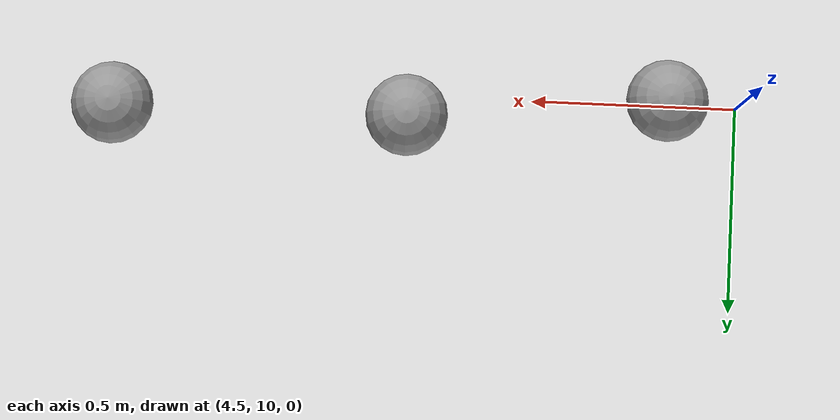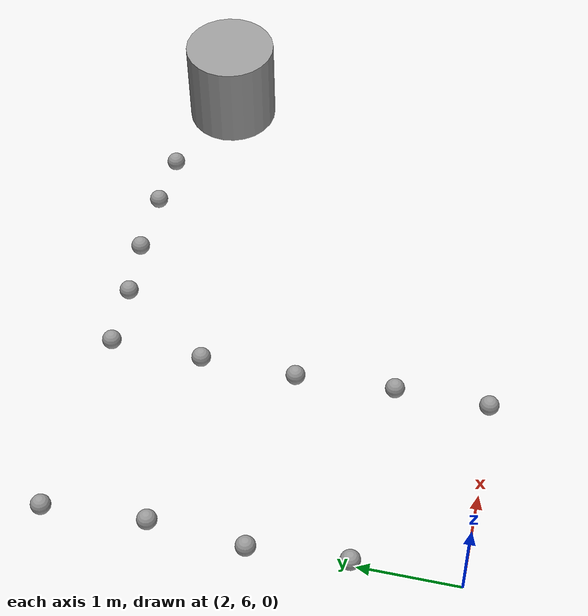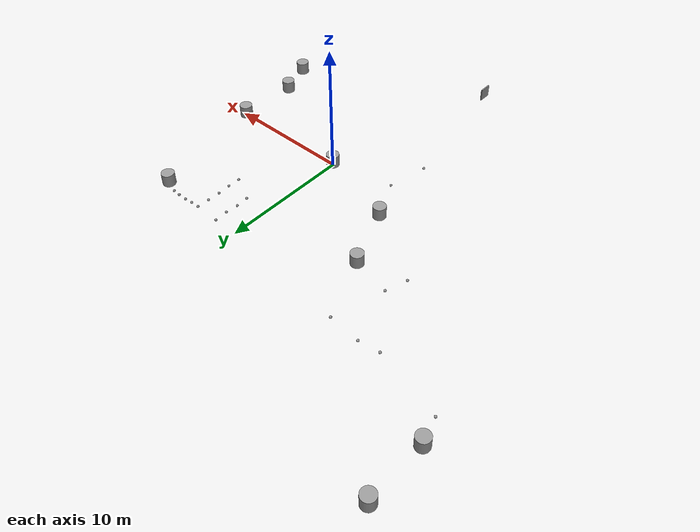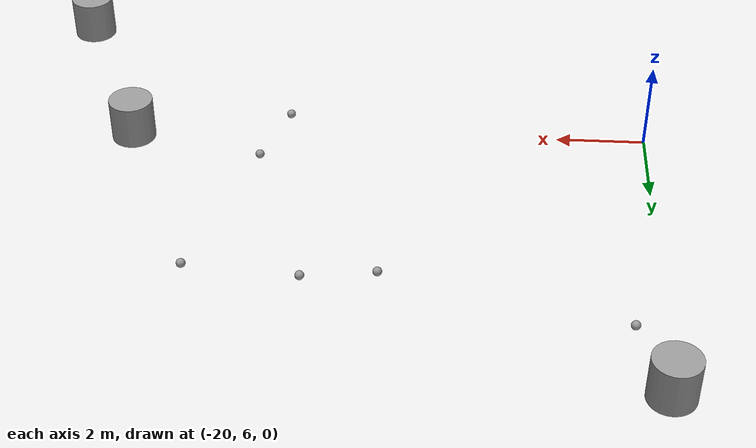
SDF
<sdf version="1.7">
 <world name="default">
  <light name="sun" type="directional">
   <pose>0 0 10 0 -0 0</pose>
   <diffuse>0.8 0.8 0.8 1</diffuse>
   <specular>0.2 0.2 0.2 1</specular>
   <attenuation>
    <range>1000</range>
    <constant>0.9</constant>
    <linear>0.01</linear>
    <quadratic>0.001</quadratic>
   </attenuation>
   <direction>-0.5 0.1 -0.9</direction>
   <spot><inner_angle>0</inner_angle><outer_angle>0</outer_angle><falloff>0</falloff></spot>
  </light>
  <model name="ground_plane">
   <static>1</static>
   <link name="link">
    <collision name="collision">
     <geometry><plane><normal>0 0 1</normal><size>100 100</size></plane></geometry>
     <surface><friction><ode><mu>100</mu><mu2>50</mu2></ode></friction></surface>
    </collision>
    <visual name="visual">
     <cast_shadows>0</cast_shadows>
     <geometry><plane><normal>0 0 1</normal><size>100 100</size></plane></geometry>
     <material>
      <script><uri>file://media/materials/scripts/gazebo.material</uri><name>Gazebo/White</name></script>
     </material>
    </visual>
   </link>
  </model>
  <gravity>0 0 -9.8</gravity>
  <magnetic_field>6e-06 2.3e-05 -4.2e-05</magnetic_field>
  <atmosphere type="adiabatic"/>
  <physics type="ode">
   <max_step_size>0.001</max_step_size>
   <real_time_factor>1</real_time_factor>
   <real_time_update_rate>1000</real_time_update_rate>
  </physics>
  <scene><ambient>0.4 0.4 0.4 1</ambient><background>0.7 0.7 0.7 1</background><shadows>1</shadows></scene>
  <spherical_coordinates>
   <surface_model>EARTH_WGS84</surface_model>
   <latitude_deg>0</latitude_deg>
   <longitude_deg>0</longitude_deg>
   <elevation>0</elevation>
   <heading_deg>0</heading_deg>
  </spherical_coordinates>
  <model name="model2.10">
   <link name="link_12">
    <inertial>
     <mass>1</mass>
     <inertia><ixx>0.145833</ixx><ixy>0</ixy><ixz>0</ixz><iyy>0.145833</iyy><iyz>0</iyz><izz>0.125</izz></inertia>
    </inertial>
    <pose>-3e-06 1e-06 0 0 -0 0</pose>
    <visual name="visual">
     <geometry><cylinder><radius>0.5</radius><length>1</length></cylinder></geometry>
     <material>
      <lighting>1</lighting>
      <script><uri>file://media/materials/scripts/gazebo.material</uri><name>Gazebo/Grey</name></script>
      <shader type="pixel"/>
     </material>
    </visual>
    <collision name="collision">
     <geometry><cylinder><radius>0.5</radius><length>1</length></cylinder></geometry>
     <surface>
      <friction>
       <ode><mu>1</mu><mu2>1</mu2><fdir1>0 0 0</fdir1><slip1>0</slip1><slip2>0</slip2></ode>
       <torsional>
        <coefficient>1</coefficient>
        <patch_radius>0</patch_radius>
        <surface_radius>0</surface_radius>
        <use_patch_radius>1</use_patch_radius>
        <ode><slip>0</slip></ode>
       </torsional>
      </friction>
      <bounce><restitution_coefficient>0</restitution_coefficient><threshold>1e+06</threshold></bounce>
      <contact>
       <collide_without_contact>0</collide_without_contact>
       <collide_without_contact_bitmask>1</collide_without_contact_bitmask>
       <collide_bitmask>1</collide_bitmask>
       <ode>
        <soft_cfm>0</soft_cfm>
        <soft_erp>0.2</soft_erp>
        <kp>1e+13</kp>
        <kd>1</kd>
        <max_vel>0</max_vel>
        <min_depth>0.001</min_depth>
       </ode>
       <bullet>
        <split_impulse>1</split_impulse>
        <split_impulse_penetration_threshold>-0.01</split_impulse_penetration_threshold>
        <soft_cfm>0</soft_cfm>
        <soft_erp>0.2</soft_erp>
        <kp>1e+13</kp>
        <kd>1</kd>
       </bullet>
      </contact>
     </surface>
    </collision>
   </link>
   <static>0</static>
   <pose>-19.8516 18.6295 0.499 0 -0 0</pose>
  </model>
  <model name="model2.1">
   <link name="link_0">
    <inertial>
     <mass>1</mass>
     <inertia><ixx>0.145833</ixx><ixy>0</ixy><ixz>0</ixz><iyy>0.145833</iyy><iyz>0</iyz><izz>0.125</izz></inertia>
    </inertial>
    <visual name="visual">
     <geometry><cylinder><radius>0.5</radius><length>1</length></cylinder></geometry>
     <material>
      <lighting>1</lighting>
      <script><uri>file://media/materials/scripts/gazebo.material</uri><name>Gazebo/Grey</name></script>
      <shader type="pixel"><normal_map>__default__</normal_map></shader>
     </material>
    </visual>
    <collision name="collision">
     <geometry><cylinder><radius>0.5</radius><length>1</length></cylinder></geometry>
     <surface>
      <friction>
       <ode><mu>1</mu><mu2>1</mu2><fdir1>0 0 0</fdir1><slip1>0</slip1><slip2>0</slip2></ode>
       <torsional>
        <coefficient>1</coefficient>
        <patch_radius>0</patch_radius>
        <surface_radius>0</surface_radius>
        <use_patch_radius>1</use_patch_radius>
        <ode><slip>0</slip></ode>
       </torsional>
      </friction>
      <bounce><restitution_coefficient>0</restitution_coefficient><threshold>1e+06</threshold></bounce>
      <contact>
       <collide_without_contact>0</collide_without_contact>
       <collide_without_contact_bitmask>1</collide_without_contact_bitmask>
       <collide_bitmask>1</collide_bitmask>
       <ode>
        <soft_cfm>0</soft_cfm>
        <soft_erp>0.2</soft_erp>
        <kp>1e+13</kp>
        <kd>1</kd>
        <max_vel>0</max_vel>
        <min_depth>0.001</min_depth>
       </ode>
       <bullet>
        <split_impulse>1</split_impulse>
        <split_impulse_penetration_threshold>-0.01</split_impulse_penetration_threshold>
        <soft_cfm>0</soft_cfm>
        <soft_erp>0.2</soft_erp>
        <kp>1e+13</kp>
        <kd>1</kd>
       </bullet>
      </contact>
     </surface>
    </collision>
   </link>
   <static>0</static>
   <pose>-6.38449 1.9957 0.499245 0.000173 0.000384 0.050783</pose>
  </model>
  <model name="model2.2">
   <link name="link_1">
    <inertial>
     <mass>1</mass>
     <inertia><ixx>0.145833</ixx><ixy>0</ixy><ixz>0</ixz><iyy>0.145833</iyy><iyz>0</iyz><izz>0.125</izz></inertia>
    </inertial>
    <pose>0 5e-06 0 0 -0 0</pose>
    <visual name="visual">
     <geometry><cylinder><radius>0.5</radius><length>1</length></cylinder></geometry>
     <material>
      <lighting>1</lighting>
      <script><uri>file://media/materials/scripts/gazebo.material</uri><name>Gazebo/Grey</name></script>
      <shader type="pixel"/>
     </material>
    </visual>
    <collision name="collision">
     <geometry><cylinder><radius>0.5</radius><length>1</length></cylinder></geometry>
     <surface>
      <friction>
       <ode><mu>1</mu><mu2>1</mu2><fdir1>0 0 0</fdir1><slip1>0</slip1><slip2>0</slip2></ode>
       <torsional>
        <coefficient>1</coefficient>
        <patch_radius>0</patch_radius>
        <surface_radius>0</surface_radius>
        <use_patch_radius>1</use_patch_radius>
        <ode><slip>0</slip></ode>
       </torsional>
      </friction>
      <bounce><restitution_coefficient>0</restitution_coefficient><threshold>1e+06</threshold></bounce>
      <contact>
       <collide_without_contact>0</collide_without_contact>
       <collide_without_contact_bitmask>1</collide_without_contact_bitmask>
       <collide_bitmask>1</collide_bitmask>
       <ode>
        <soft_cfm>0</soft_cfm>
        <soft_erp>0.2</soft_erp>
        <kp>1e+13</kp>
        <kd>1</kd>
        <max_vel>0</max_vel>
        <min_depth>0.001</min_depth>
       </ode>
       <bullet>
        <split_impulse>1</split_impulse>
        <split_impulse_penetration_threshold>-0.01</split_impulse_penetration_threshold>
        <soft_cfm>0</soft_cfm>
        <soft_erp>0.2</soft_erp>
        <kp>1e+13</kp>
        <kd>1</kd>
       </bullet>
      </contact>
     </surface>
    </collision>
   </link>
   <static>0</static>
   <pose>0.015888 -0.015142 0.499 0 0 -0.646755</pose>
  </model>
  <model name="model2.4">
   <link name="link_4">
    <inertial>
     <mass>1</mass>
     <inertia><ixx>0.145833</ixx><ixy>0</ixy><ixz>0</ixz><iyy>0.145833</iyy><iyz>0</iyz><izz>0.125</izz></inertia>
    </inertial>
    <pose>-3e-06 0 0 0 -0 0</pose>
    <visual name="visual">
     <geometry><cylinder><radius>0.5</radius><length>1</length></cylinder></geometry>
     <material>
      <lighting>1</lighting>
      <script><uri>file://media/materials/scripts/gazebo.material</uri><name>Gazebo/Grey</name></script>
      <shader type="pixel"/>
     </material>
    </visual>
    <collision name="collision">
     <geometry><cylinder><radius>0.5</radius><length>1</length></cylinder></geometry>
     <surface>
      <friction>
       <ode><mu>1</mu><mu2>1</mu2><fdir1>0 0 0</fdir1><slip1>0</slip1><slip2>0</slip2></ode>
       <torsional>
        <coefficient>1</coefficient>
        <patch_radius>0</patch_radius>
        <surface_radius>0</surface_radius>
        <use_patch_radius>1</use_patch_radius>
        <ode><slip>0</slip></ode>
       </torsional>
      </friction>
      <bounce><restitution_coefficient>0</restitution_coefficient><threshold>1e+06</threshold></bounce>
      <contact>
       <collide_without_contact>0</collide_without_contact>
       <collide_without_contact_bitmask>1</collide_without_contact_bitmask>
       <collide_bitmask>1</collide_bitmask>
       <ode>
        <soft_cfm>0</soft_cfm>
        <soft_erp>0.2</soft_erp>
        <kp>1e+13</kp>
        <kd>1</kd>
        <max_vel>0</max_vel>
        <min_depth>0.001</min_depth>
       </ode>
       <bullet>
        <split_impulse>1</split_impulse>
        <split_impulse_penetration_threshold>-0.01</split_impulse_penetration_threshold>
        <soft_cfm>0</soft_cfm>
        <soft_erp>0.2</soft_erp>
        <kp>1e+13</kp>
        <kd>1</kd>
       </bullet>
      </contact>
     </surface>
    </collision>
   </link>
   <static>0</static>
   <pose>-19.9097 14.1982 0.499 0 -0 0</pose>
  </model>
  <model name="model2.3">
   <link name="link_11">
    <inertial>
     <mass>1</mass>
     <inertia><ixx>0.145833</ixx><ixy>0</ixy><ixz>0</ixz><iyy>0.145833</iyy><iyz>0</iyz><izz>0.125</izz></inertia>
    </inertial>
    <pose>-3e-06 0 0 0 -0 0</pose>
    <visual name="visual">
     <geometry><cylinder><radius>0.5</radius><length>1</length></cylinder></geometry>
     <material>
      <lighting>1</lighting>
      <script><uri>file://media/materials/scripts/gazebo.material</uri><name>Gazebo/Grey</name></script>
      <shader type="pixel"/>
     </material>
    </visual>
    <collision name="collision">
     <geometry><cylinder><radius>0.5</radius><length>1</length></cylinder></geometry>
     <surface>
      <friction>
       <ode><mu>1</mu><mu2>1</mu2><fdir1>0 0 0</fdir1><slip1>0</slip1><slip2>0</slip2></ode>
       <torsional>
        <coefficient>1</coefficient>
        <patch_radius>0</patch_radius>
        <surface_radius>0</surface_radius>
        <use_patch_radius>1</use_patch_radius>
        <ode><slip>0</slip></ode>
       </torsional>
      </friction>
      <bounce><restitution_coefficient>0</restitution_coefficient><threshold>1e+06</threshold></bounce>
      <contact>
       <collide_without_contact>0</collide_without_contact>
       <collide_without_contact_bitmask>1</collide_without_contact_bitmask>
       <collide_bitmask>1</collide_bitmask>
       <ode>
        <soft_cfm>0</soft_cfm>
        <soft_erp>0.2</soft_erp>
        <kp>1e+13</kp>
        <kd>1</kd>
        <max_vel>0</max_vel>
        <min_depth>0.001</min_depth>
       </ode>
       <bullet>
        <split_impulse>1</split_impulse>
        <split_impulse_penetration_threshold>-0.01</split_impulse_penetration_threshold>
        <soft_cfm>0</soft_cfm>
        <soft_erp>0.2</soft_erp>
        <kp>1e+13</kp>
        <kd>1</kd>
       </bullet>
      </contact>
     </surface>
    </collision>
   </link>
   <static>0</static>
   <pose>9.68378 0.021997 0.499 0 -0 0</pose>
  </model>
  <model name="model2.5">
   <link name="link_5">
    <inertial>
     <mass>1</mass>
     <inertia><ixx>0.145833</ixx><ixy>0</ixy><ixz>0</ixz><iyy>0.145833</iyy><iyz>0</iyz><izz>0.125</izz></inertia>
    </inertial>
    <pose>-0 4e-06 0 0 -0 0</pose>
    <visual name="visual">
     <geometry><cylinder><radius>0.5</radius><length>1</length></cylinder></geometry>
     <material>
      <lighting>1</lighting>
      <script><uri>file://media/materials/scripts/gazebo.material</uri><name>Gazebo/Grey</name></script>
      <shader type="pixel"/>
     </material>
    </visual>
    <collision name="collision">
     <geometry><cylinder><radius>0.5</radius><length>1</length></cylinder></geometry>
     <surface>
      <friction>
       <ode><mu>1</mu><mu2>1</mu2><fdir1>0 0 0</fdir1><slip1>0</slip1><slip2>0</slip2></ode>
       <torsional>
        <coefficient>1</coefficient>
        <patch_radius>0</patch_radius>
        <surface_radius>0</surface_radius>
        <use_patch_radius>1</use_patch_radius>
        <ode><slip>0</slip></ode>
       </torsional>
      </friction>
      <bounce><restitution_coefficient>0</restitution_coefficient><threshold>1e+06</threshold></bounce>
      <contact>
       <collide_without_contact>0</collide_without_contact>
       <collide_without_contact_bitmask>1</collide_without_contact_bitmask>
       <collide_bitmask>1</collide_bitmask>
       <ode>
        <soft_cfm>0</soft_cfm>
        <soft_erp>0.2</soft_erp>
        <kp>1e+13</kp>
        <kd>1</kd>
        <max_vel>0</max_vel>
        <min_depth>0.001</min_depth>
       </ode>
       <bullet>
        <split_impulse>1</split_impulse>
        <split_impulse_penetration_threshold>-0.01</split_impulse_penetration_threshold>
        <soft_cfm>0</soft_cfm>
        <soft_erp>0.2</soft_erp>
        <kp>1e+13</kp>
        <kd>1</kd>
       </bullet>
      </contact>
     </surface>
    </collision>
   </link>
   <static>0</static>
   <pose>-8.23961 6.46008 0.499 0 -0 0</pose>
  </model>
  <model name="model2.6">
   <link name="link_6">
    <inertial>
     <mass>1</mass>
     <inertia><ixx>0.145833</ixx><ixy>0</ixy><ixz>0</ixz><iyy>0.145833</iyy><iyz>0</iyz><izz>0.125</izz></inertia>
    </inertial>
    <pose>-4e-06 4e-06 0 0 -0 0</pose>
    <visual name="visual">
     <geometry><cylinder><radius>0.5</radius><length>1</length></cylinder></geometry>
     <material>
      <lighting>1</lighting>
      <script><uri>file://media/materials/scripts/gazebo.material</uri><name>Gazebo/Grey</name></script>
      <shader type="pixel"/>
     </material>
    </visual>
    <collision name="collision">
     <geometry><cylinder><radius>0.5</radius><length>1</length></cylinder></geometry>
     <surface>
      <friction>
       <ode><mu>1</mu><mu2>1</mu2><fdir1>0 0 0</fdir1><slip1>0</slip1><slip2>0</slip2></ode>
       <torsional>
        <coefficient>1</coefficient>
        <patch_radius>0</patch_radius>
        <surface_radius>0</surface_radius>
        <use_patch_radius>1</use_patch_radius>
        <ode><slip>0</slip></ode>
       </torsional>
      </friction>
      <bounce><restitution_coefficient>0</restitution_coefficient><threshold>1e+06</threshold></bounce>
      <contact>
       <collide_without_contact>0</collide_without_contact>
       <collide_without_contact_bitmask>1</collide_without_contact_bitmask>
       <collide_bitmask>1</collide_bitmask>
       <ode>
        <soft_cfm>0</soft_cfm>
        <soft_erp>0.2</soft_erp>
        <kp>1e+13</kp>
        <kd>1</kd>
        <max_vel>0</max_vel>
        <min_depth>0.001</min_depth>
       </ode>
       <bullet>
        <split_impulse>1</split_impulse>
        <split_impulse_penetration_threshold>-0.01</split_impulse_penetration_threshold>
        <soft_cfm>0</soft_cfm>
        <soft_erp>0.2</soft_erp>
        <kp>1e+13</kp>
        <kd>1</kd>
       </bullet>
      </contact>
     </surface>
    </collision>
   </link>
   <static>0</static>
   <pose>9.63794 -4.80031 0.499 0 -0 0</pose>
  </model>
  <model name="model2.7">
   <link name="link_7">
    <inertial>
     <mass>1</mass>
     <inertia><ixx>0.145833</ixx><ixy>0</ixy><ixz>0</ixz><iyy>0.145833</iyy><iyz>0</iyz><izz>0.125</izz></inertia>
    </inertial>
    <pose>4.2e-05 4e-06 0 0 -0 0</pose>
    <visual name="visual">
     <geometry><cylinder><radius>0.5</radius><length>1</length></cylinder></geometry>
     <material>
      <lighting>1</lighting>
      <script><uri>file://media/materials/scripts/gazebo.material</uri><name>Gazebo/Grey</name></script>
      <shader type="pixel"/>
     </material>
    </visual>
    <collision name="collision">
     <geometry><cylinder><radius>0.5</radius><length>1</length></cylinder></geometry>
     <surface>
      <friction>
       <ode><mu>1</mu><mu2>1</mu2><fdir1>0 0 0</fdir1><slip1>0</slip1><slip2>0</slip2></ode>
       <torsional>
        <coefficient>1</coefficient>
        <patch_radius>0</patch_radius>
        <surface_radius>0</surface_radius>
        <use_patch_radius>1</use_patch_radius>
        <ode><slip>0</slip></ode>
       </torsional>
      </friction>
      <bounce><restitution_coefficient>0</restitution_coefficient><threshold>1e+06</threshold></bounce>
      <contact>
       <collide_without_contact>0</collide_without_contact>
       <collide_without_contact_bitmask>1</collide_without_contact_bitmask>
       <collide_bitmask>1</collide_bitmask>
       <ode>
        <soft_cfm>0</soft_cfm>
        <soft_erp>0.2</soft_erp>
        <kp>1e+13</kp>
        <kd>1</kd>
        <max_vel>0</max_vel>
        <min_depth>0.001</min_depth>
       </ode>
       <bullet>
        <split_impulse>1</split_impulse>
        <split_impulse_penetration_threshold>-0.01</split_impulse_penetration_threshold>
        <soft_cfm>0</soft_cfm>
        <soft_erp>0.2</soft_erp>
        <kp>1e+13</kp>
        <kd>1</kd>
       </bullet>
      </contact>
     </surface>
    </collision>
   </link>
   <static>0</static>
   <pose>680.257 352.705 0.499899 -1.57086 -1.21827 0.481976</pose>
  </model>
  <model name="model2.8">
   <link name="link_8">
    <inertial>
     <mass>1</mass>
     <inertia><ixx>0.145833</ixx><ixy>0</ixy><ixz>0</ixz><iyy>0.145833</iyy><iyz>0</iyz><izz>0.125</izz></inertia>
    </inertial>
    <pose>0 4e-06 0 0 -0 0</pose>
    <visual name="visual">
     <geometry><cylinder><radius>0.5</radius><length>1</length></cylinder></geometry>
     <material>
      <lighting>1</lighting>
      <script><uri>file://media/materials/scripts/gazebo.material</uri><name>Gazebo/Grey</name></script>
      <shader type="pixel"/>
     </material>
    </visual>
    <collision name="collision">
     <geometry><cylinder><radius>0.5</radius><length>1</length></cylinder></geometry>
     <surface>
      <friction>
       <ode><mu>1</mu><mu2>1</mu2><fdir1>0 0 0</fdir1><slip1>0</slip1><slip2>0</slip2></ode>
       <torsional>
        <coefficient>1</coefficient>
        <patch_radius>0</patch_radius>
        <surface_radius>0</surface_radius>
        <use_patch_radius>1</use_patch_radius>
        <ode><slip>0</slip></ode>
       </torsional>
      </friction>
      <bounce><restitution_coefficient>0</restitution_coefficient><threshold>1e+06</threshold></bounce>
      <contact>
       <collide_without_contact>0</collide_without_contact>
       <collide_without_contact_bitmask>1</collide_without_contact_bitmask>
       <collide_bitmask>1</collide_bitmask>
       <ode>
        <soft_cfm>0</soft_cfm>
        <soft_erp>0.2</soft_erp>
        <kp>1e+13</kp>
        <kd>1</kd>
        <max_vel>0</max_vel>
        <min_depth>0.001</min_depth>
       </ode>
       <bullet>
        <split_impulse>1</split_impulse>
        <split_impulse_penetration_threshold>-0.01</split_impulse_penetration_threshold>
        <soft_cfm>0</soft_cfm>
        <soft_erp>0.2</soft_erp>
        <kp>1e+13</kp>
        <kd>1</kd>
       </bullet>
      </contact>
     </surface>
    </collision>
   </link>
   <static>0</static>
   <pose>10.732 -7.6295 0.499 0 -0 0</pose>
  </model>
  <model name="model2.9">
   <link name="link_9">
    <inertial>
     <mass>1</mass>
     <inertia><ixx>0.145833</ixx><ixy>0</ixy><ixz>0</ixz><iyy>0.145833</iyy><iyz>0</iyz><izz>0.125</izz></inertia>
    </inertial>
    <pose>3e-06 1e-06 0 0 -0 0</pose>
    <visual name="visual">
     <geometry><cylinder><radius>0.5</radius><length>1</length></cylinder></geometry>
     <material>
      <lighting>1</lighting>
      <script><uri>file://media/materials/scripts/gazebo.material</uri><name>Gazebo/Grey</name></script>
      <shader type="pixel"/>
     </material>
    </visual>
    <collision name="collision">
     <geometry><cylinder><radius>0.5</radius><length>1</length></cylinder></geometry>
     <surface>
      <friction>
       <ode><mu>1</mu><mu2>1</mu2><fdir1>0 0 0</fdir1><slip1>0</slip1><slip2>0</slip2></ode>
       <torsional>
        <coefficient>1</coefficient>
        <patch_radius>0</patch_radius>
        <surface_radius>0</surface_radius>
        <use_patch_radius>1</use_patch_radius>
        <ode><slip>0</slip></ode>
       </torsional>
      </friction>
      <bounce><restitution_coefficient>0</restitution_coefficient><threshold>1e+06</threshold></bounce>
      <contact>
       <collide_without_contact>0</collide_without_contact>
       <collide_without_contact_bitmask>1</collide_without_contact_bitmask>
       <collide_bitmask>1</collide_bitmask>
       <ode>
        <soft_cfm>0</soft_cfm>
        <soft_erp>0.2</soft_erp>
        <kp>1e+13</kp>
        <kd>1</kd>
        <max_vel>0</max_vel>
        <min_depth>0.001</min_depth>
       </ode>
       <bullet>
        <split_impulse>1</split_impulse>
        <split_impulse_penetration_threshold>-0.01</split_impulse_penetration_threshold>
        <soft_cfm>0</soft_cfm>
        <soft_erp>0.2</soft_erp>
        <kp>1e+13</kp>
        <kd>1</kd>
       </bullet>
      </contact>
     </surface>
    </collision>
   </link>
   <static>0</static>
   <pose>7.68386 9.62616 0.499 0 -0 0</pose>
  </model>
  <model name="sphere">
   <link name="link_0">
    <inertial>
     <mass>1</mass>
     <inertia><ixx>0.1</ixx><ixy>0</ixy><ixz>0</ixz><iyy>0.1</iyy><iyz>0</iyz><izz>0.1</izz></inertia>
    </inertial>
    <visual name="visual">
     <geometry><sphere><radius>0.1</radius></sphere></geometry>
     <material>
      <lighting>1</lighting>
      <script><uri>file://media/materials/scripts/gazebo.material</uri><name>Gazebo/Grey</name></script>
      <shader type="pixel"><normal_map>__default__</normal_map></shader>
      <ambient>0.3 0.3 0.3 1</ambient>
      <diffuse>0.7 0.7 0.7 1</diffuse>
      <specular>0.01 0.01 0.01 1</specular>
      <emissive>0 0 0 1</emissive>
     </material>
    </visual>
    <collision name="collision">
     <geometry><sphere><radius>0.1</radius></sphere></geometry>
     <surface>
      <friction>
       <ode><mu>1</mu><mu2>1</mu2><fdir1>0 0 0</fdir1><slip1>0</slip1><slip2>0</slip2></ode>
       <torsional>
        <coefficient>1</coefficient>
        <patch_radius>0</patch_radius>
        <surface_radius>0</surface_radius>
        <use_patch_radius>1</use_patch_radius>
        <ode><slip>0</slip></ode>
       </torsional>
      </friction>
      <bounce><restitution_coefficient>0</restitution_coefficient><threshold>1e+06</threshold></bounce>
      <contact>
       <collide_without_contact>0</collide_without_contact>
       <collide_without_contact_bitmask>1</collide_without_contact_bitmask>
       <collide_bitmask>1</collide_bitmask>
       <ode>
        <soft_cfm>0</soft_cfm>
        <soft_erp>0.2</soft_erp>
        <kp>1e+13</kp>
        <kd>1</kd>
        <max_vel>0.01</max_vel>
        <min_depth>0</min_depth>
       </ode>
       <bullet>
        <split_impulse>1</split_impulse>
        <split_impulse_penetration_threshold>-0.01</split_impulse_penetration_threshold>
        <soft_cfm>0</soft_cfm>
        <soft_erp>0.2</soft_erp>
        <kp>1e+13</kp>
        <kd>1</kd>
       </bullet>
      </contact>
     </surface>
    </collision>
   </link>
   <static>0</static>
   <pose>-14.1838 11.056 0.1 -0.015918 -0.013577 -6e-05</pose>
  </model>
  <model name="wall1.1">
   <link name="link_0">
    <inertial>
     <mass>1</mass>
     <inertia>
      <ixx>0.166667</ixx>
      <ixy>0</ixy>
      <ixz>0</ixz>
      <iyy>0.166667</iyy>
      <iyz>0</iyz>
      <izz>0.166667</izz>
     </inertia>
    </inertial>
    <visual name="visual">
     <geometry><box><size>0.1 1 1</size></box></geometry>
     <material>
      <lighting>1</lighting>
      <script><uri>file://media/materials/scripts/gazebo.material</uri><name>Gazebo/Grey</name></script>
      <shader type="pixel"><normal_map>__default__</normal_map></shader>
      <ambient>0.3 0.3 0.3 1</ambient>
      <diffuse>0.7 0.7 0.7 1</diffuse>
      <specular>0.01 0.01 0.01 1</specular>
      <emissive>0 0 0 1</emissive>
     </material>
    </visual>
    <collision name="collision">
     <geometry><box><size>0.1 1 1</size></box></geometry>
     <surface>
      <friction>
       <ode><mu>1</mu><mu2>1</mu2><fdir1>0 0 0</fdir1><slip1>0</slip1><slip2>0</slip2></ode>
       <torsional>
        <coefficient>1</coefficient>
        <patch_radius>0</patch_radius>
        <surface_radius>0</surface_radius>
        <use_patch_radius>1</use_patch_radius>
        <ode><slip>0</slip></ode>
       </torsional>
      </friction>
      <bounce><restitution_coefficient>0</restitution_coefficient><threshold>1e+06</threshold></bounce>
      <contact>
       <collide_without_contact>0</collide_without_contact>
       <collide_without_contact_bitmask>1</collide_without_contact_bitmask>
       <collide_bitmask>1</collide_bitmask>
       <ode>
        <soft_cfm>0</soft_cfm>
        <soft_erp>0.2</soft_erp>
        <kp>1e+13</kp>
        <kd>1</kd>
        <max_vel>0.01</max_vel>
        <min_depth>0</min_depth>
       </ode>
       <bullet>
        <split_impulse>1</split_impulse>
        <split_impulse_penetration_threshold>-0.01</split_impulse_penetration_threshold>
        <soft_cfm>0</soft_cfm>
        <soft_erp>0.2</soft_erp>
        <kp>1e+13</kp>
        <kd>1</kd>
       </bullet>
      </contact>
     </surface>
    </collision>
   </link>
   <static>0</static>
   <pose>-3.59478 -14.9365 0.5 -0 -0 -2.3e-05</pose>
  </model>
  <model name="sphere_0">
   <link name="link_0">
    <inertial>
     <mass>1</mass>
     <inertia><ixx>0.1</ixx><ixy>0</ixy><ixz>0</ixz><iyy>0.1</iyy><iyz>0</iyz><izz>0.1</izz></inertia>
    </inertial>
    <visual name="visual">
     <geometry><sphere><radius>0.1</radius></sphere></geometry>
     <material>
      <lighting>1</lighting>
      <script><uri>file://media/materials/scripts/gazebo.material</uri><name>Gazebo/Grey</name></script>
      <shader type="pixel"><normal_map>__default__</normal_map></shader>
      <ambient>0.3 0.3 0.3 1</ambient>
      <diffuse>0.7 0.7 0.7 1</diffuse>
      <specular>0.01 0.01 0.01 1</specular>
      <emissive>0 0 0 1</emissive>
     </material>
    </visual>
    <collision name="collision">
     <geometry><sphere><radius>0.1</radius></sphere></geometry>
     <surface>
      <friction>
       <ode><mu>1</mu><mu2>1</mu2><fdir1>0 0 0</fdir1><slip1>0</slip1><slip2>0</slip2></ode>
       <torsional>
        <coefficient>1</coefficient>
        <patch_radius>0</patch_radius>
        <surface_radius>0</surface_radius>
        <use_patch_radius>1</use_patch_radius>
        <ode><slip>0</slip></ode>
       </torsional>
      </friction>
      <bounce><restitution_coefficient>0</restitution_coefficient><threshold>1e+06</threshold></bounce>
      <contact>
       <collide_without_contact>0</collide_without_contact>
       <collide_without_contact_bitmask>1</collide_without_contact_bitmask>
       <collide_bitmask>1</collide_bitmask>
       <ode>
        <soft_cfm>0</soft_cfm>
        <soft_erp>0.2</soft_erp>
        <kp>1e+13</kp>
        <kd>1</kd>
        <max_vel>0.01</max_vel>
        <min_depth>0</min_depth>
       </ode>
       <bullet>
        <split_impulse>1</split_impulse>
        <split_impulse_penetration_threshold>-0.01</split_impulse_penetration_threshold>
        <soft_cfm>0</soft_cfm>
        <soft_erp>0.2</soft_erp>
        <kp>1e+13</kp>
        <kd>1</kd>
       </bullet>
      </contact>
     </surface>
    </collision>
   </link>
   <static>0</static>
   <pose>-11.7981 5.50129 0.1 -0.35685 -0.138799 0.018482</pose>
  </model>
  <model name="sphere_1">
   <link name="link_0">
    <inertial>
     <mass>1</mass>
     <inertia><ixx>0.1</ixx><ixy>0</ixy><ixz>0</ixz><iyy>0.1</iyy><iyz>0</iyz><izz>0.1</izz></inertia>
    </inertial>
    <visual name="visual">
     <geometry><sphere><radius>0.1</radius></sphere></geometry>
     <material>
      <lighting>1</lighting>
      <script><uri>file://media/materials/scripts/gazebo.material</uri><name>Gazebo/Grey</name></script>
      <shader type="pixel"><normal_map>__default__</normal_map></shader>
      <ambient>0.3 0.3 0.3 1</ambient>
      <diffuse>0.7 0.7 0.7 1</diffuse>
      <specular>0.01 0.01 0.01 1</specular>
      <emissive>0 0 0 1</emissive>
     </material>
    </visual>
    <collision name="collision">
     <geometry><sphere><radius>0.1</radius></sphere></geometry>
     <surface>
      <friction>
       <ode><mu>1</mu><mu2>1</mu2><fdir1>0 0 0</fdir1><slip1>0</slip1><slip2>0</slip2></ode>
       <torsional>
        <coefficient>1</coefficient>
        <patch_radius>0</patch_radius>
        <surface_radius>0</surface_radius>
        <use_patch_radius>1</use_patch_radius>
        <ode><slip>0</slip></ode>
       </torsional>
      </friction>
      <bounce><restitution_coefficient>0</restitution_coefficient><threshold>1e+06</threshold></bounce>
      <contact>
       <collide_without_contact>0</collide_without_contact>
       <collide_without_contact_bitmask>1</collide_without_contact_bitmask>
       <collide_bitmask>1</collide_bitmask>
       <ode>
        <soft_cfm>0</soft_cfm>
        <soft_erp>0.2</soft_erp>
        <kp>1e+13</kp>
        <kd>1</kd>
        <max_vel>0.01</max_vel>
        <min_depth>0</min_depth>
       </ode>
       <bullet>
        <split_impulse>1</split_impulse>
        <split_impulse_penetration_threshold>-0.01</split_impulse_penetration_threshold>
        <soft_cfm>0</soft_cfm>
        <soft_erp>0.2</soft_erp>
        <kp>1e+13</kp>
        <kd>1</kd>
       </bullet>
      </contact>
     </surface>
    </collision>
   </link>
   <static>0</static>
   <pose>-11.2616 7.14077 0.1 0 -0 0</pose>
  </model>
  <model name="sphere_2">
   <link name="link_0">
    <inertial>
     <mass>1</mass>
     <inertia><ixx>0.1</ixx><ixy>0</ixy><ixz>0</ixz><iyy>0.1</iyy><iyz>0</iyz><izz>0.1</izz></inertia>
    </inertial>
    <visual name="visual">
     <geometry><sphere><radius>0.1</radius></sphere></geometry>
     <material>
      <lighting>1</lighting>
      <script><uri>file://media/materials/scripts/gazebo.material</uri><name>Gazebo/Grey</name></script>
      <shader type="pixel"><normal_map>__default__</normal_map></shader>
      <ambient>0.3 0.3 0.3 1</ambient>
      <diffuse>0.7 0.7 0.7 1</diffuse>
      <specular>0.01 0.01 0.01 1</specular>
      <emissive>0 0 0 1</emissive>
     </material>
    </visual>
    <collision name="collision">
     <geometry><sphere><radius>0.1</radius></sphere></geometry>
     <surface>
      <friction>
       <ode><mu>1</mu><mu2>1</mu2><fdir1>0 0 0</fdir1><slip1>0</slip1><slip2>0</slip2></ode>
       <torsional>
        <coefficient>1</coefficient>
        <patch_radius>0</patch_radius>
        <surface_radius>0</surface_radius>
        <use_patch_radius>1</use_patch_radius>
        <ode><slip>0</slip></ode>
       </torsional>
      </friction>
      <bounce><restitution_coefficient>0</restitution_coefficient><threshold>1e+06</threshold></bounce>
      <contact>
       <collide_without_contact>0</collide_without_contact>
       <collide_without_contact_bitmask>1</collide_without_contact_bitmask>
       <collide_bitmask>1</collide_bitmask>
       <ode>
        <soft_cfm>0</soft_cfm>
        <soft_erp>0.2</soft_erp>
        <kp>1e+13</kp>
        <kd>1</kd>
        <max_vel>0.01</max_vel>
        <min_depth>0</min_depth>
       </ode>
       <bullet>
        <split_impulse>1</split_impulse>
        <split_impulse_penetration_threshold>-0.01</split_impulse_penetration_threshold>
        <soft_cfm>0</soft_cfm>
        <soft_erp>0.2</soft_erp>
        <kp>1e+13</kp>
        <kd>1</kd>
       </bullet>
      </contact>
     </surface>
    </collision>
   </link>
   <static>0</static>
   <pose>-4.9525 -0.997504 0.1 -0.580739 -0.3012 -0.13872</pose>
  </model>
  <model name="sphere_3">
   <link name="link_0">
    <inertial>
     <mass>1</mass>
     <inertia><ixx>0.1</ixx><ixy>0</ixy><ixz>0</ixz><iyy>0.1</iyy><iyz>0</iyz><izz>0.1</izz></inertia>
    </inertial>
    <visual name="visual">
     <geometry><sphere><radius>0.1</radius></sphere></geometry>
     <material>
      <lighting>1</lighting>
      <script><uri>file://media/materials/scripts/gazebo.material</uri><name>Gazebo/Grey</name></script>
      <shader type="pixel"><normal_map>__default__</normal_map></shader>
      <ambient>0.3 0.3 0.3 1</ambient>
      <diffuse>0.7 0.7 0.7 1</diffuse>
      <specular>0.01 0.01 0.01 1</specular>
      <emissive>0 0 0 1</emissive>
     </material>
    </visual>
    <collision name="collision">
     <geometry><sphere><radius>0.1</radius></sphere></geometry>
     <surface>
      <friction>
       <ode><mu>1</mu><mu2>1</mu2><fdir1>0 0 0</fdir1><slip1>0</slip1><slip2>0</slip2></ode>
       <torsional>
        <coefficient>1</coefficient>
        <patch_radius>0</patch_radius>
        <surface_radius>0</surface_radius>
        <use_patch_radius>1</use_patch_radius>
        <ode><slip>0</slip></ode>
       </torsional>
      </friction>
      <bounce><restitution_coefficient>0</restitution_coefficient><threshold>1e+06</threshold></bounce>
      <contact>
       <collide_without_contact>0</collide_without_contact>
       <collide_without_contact_bitmask>1</collide_without_contact_bitmask>
       <collide_bitmask>1</collide_bitmask>
       <ode>
        <soft_cfm>0</soft_cfm>
        <soft_erp>0.2</soft_erp>
        <kp>1e+13</kp>
        <kd>1</kd>
        <max_vel>0.01</max_vel>
        <min_depth>0</min_depth>
       </ode>
       <bullet>
        <split_impulse>1</split_impulse>
        <split_impulse_penetration_threshold>-0.01</split_impulse_penetration_threshold>
        <soft_cfm>0</soft_cfm>
        <soft_erp>0.2</soft_erp>
        <kp>1e+13</kp>
        <kd>1</kd>
       </bullet>
      </contact>
     </surface>
    </collision>
   </link>
   <static>0</static>
   <pose>-5.58272 -4.148 0.1 0 -0 0</pose>
  </model>
  <model name="sphere_4">
   <link name="link_0">
    <inertial>
     <mass>1</mass>
     <inertia><ixx>0.1</ixx><ixy>0</ixy><ixz>0</ixz><iyy>0.1</iyy><iyz>0</iyz><izz>0.1</izz></inertia>
    </inertial>
    <visual name="visual">
     <geometry><sphere><radius>0.1</radius></sphere></geometry>
     <material>
      <lighting>1</lighting>
      <script><uri>file://media/materials/scripts/gazebo.material</uri><name>Gazebo/Grey</name></script>
      <shader type="pixel"><normal_map>__default__</normal_map></shader>
      <ambient>0.3 0.3 0.3 1</ambient>
      <diffuse>0.7 0.7 0.7 1</diffuse>
      <specular>0.01 0.01 0.01 1</specular>
      <emissive>0 0 0 1</emissive>
     </material>
    </visual>
    <collision name="collision">
     <geometry><sphere><radius>0.1</radius></sphere></geometry>
     <surface>
      <friction>
       <ode><mu>1</mu><mu2>1</mu2><fdir1>0 0 0</fdir1><slip1>0</slip1><slip2>0</slip2></ode>
       <torsional>
        <coefficient>1</coefficient>
        <patch_radius>0</patch_radius>
        <surface_radius>0</surface_radius>
        <use_patch_radius>1</use_patch_radius>
        <ode><slip>0</slip></ode>
       </torsional>
      </friction>
      <bounce><restitution_coefficient>0</restitution_coefficient><threshold>1e+06</threshold></bounce>
      <contact>
       <collide_without_contact>0</collide_without_contact>
       <collide_without_contact_bitmask>1</collide_without_contact_bitmask>
       <collide_bitmask>1</collide_bitmask>
       <ode>
        <soft_cfm>0</soft_cfm>
        <soft_erp>0.2</soft_erp>
        <kp>1e+13</kp>
        <kd>1</kd>
        <max_vel>0.01</max_vel>
        <min_depth>0</min_depth>
       </ode>
       <bullet>
        <split_impulse>1</split_impulse>
        <split_impulse_penetration_threshold>-0.01</split_impulse_penetration_threshold>
        <soft_cfm>0</soft_cfm>
        <soft_erp>0.2</soft_erp>
        <kp>1e+13</kp>
        <kd>1</kd>
       </bullet>
      </contact>
     </surface>
    </collision>
   </link>
   <static>0</static>
   <pose>-19.3703 12.3458 0.1 -0.29888 -0.231814 0.016243</pose>
  </model>
  <model name="sphere_5">
   <link name="link_0">
    <inertial>
     <mass>1</mass>
     <inertia><ixx>0.1</ixx><ixy>0</ixy><ixz>0</ixz><iyy>0.1</iyy><iyz>0</iyz><izz>0.1</izz></inertia>
    </inertial>
    <visual name="visual">
     <geometry><sphere><radius>0.1</radius></sphere></geometry>
     <material>
      <lighting>1</lighting>
      <script><uri>file://media/materials/scripts/gazebo.material</uri><name>Gazebo/Grey</name></script>
      <shader type="pixel"><normal_map>__default__</normal_map></shader>
      <ambient>0.3 0.3 0.3 1</ambient>
      <diffuse>0.7 0.7 0.7 1</diffuse>
      <specular>0.01 0.01 0.01 1</specular>
      <emissive>0 0 0 1</emissive>
     </material>
    </visual>
    <collision name="collision">
     <geometry><sphere><radius>0.1</radius></sphere></geometry>
     <surface>
      <friction>
       <ode><mu>1</mu><mu2>1</mu2><fdir1>0 0 0</fdir1><slip1>0</slip1><slip2>0</slip2></ode>
       <torsional>
        <coefficient>1</coefficient>
        <patch_radius>0</patch_radius>
        <surface_radius>0</surface_radius>
        <use_patch_radius>1</use_patch_radius>
        <ode><slip>0</slip></ode>
       </torsional>
      </friction>
      <bounce><restitution_coefficient>0</restitution_coefficient><threshold>1e+06</threshold></bounce>
      <contact>
       <collide_without_contact>0</collide_without_contact>
       <collide_without_contact_bitmask>1</collide_without_contact_bitmask>
       <collide_bitmask>1</collide_bitmask>
       <ode>
        <soft_cfm>0</soft_cfm>
        <soft_erp>0.2</soft_erp>
        <kp>1e+13</kp>
        <kd>1</kd>
        <max_vel>0.01</max_vel>
        <min_depth>0</min_depth>
       </ode>
       <bullet>
        <split_impulse>1</split_impulse>
        <split_impulse_penetration_threshold>-0.01</split_impulse_penetration_threshold>
        <soft_cfm>0</soft_cfm>
        <soft_erp>0.2</soft_erp>
        <kp>1e+13</kp>
        <kd>1</kd>
       </bullet>
      </contact>
     </surface>
    </collision>
   </link>
   <static>0</static>
   <pose>-12.5972 11.2791 0.1 -0.55417 0.074644 0.257656</pose>
  </model>
  <model name="sphere_6">
   <link name="link_0">
    <inertial>
     <mass>1</mass>
     <inertia><ixx>0.1</ixx><ixy>0</ixy><ixz>0</ixz><iyy>0.1</iyy><iyz>0</iyz><izz>0.1</izz></inertia>
    </inertial>
    <visual name="visual">
     <geometry><sphere><radius>0.1</radius></sphere></geometry>
     <material>
      <lighting>1</lighting>
      <script><uri>file://media/materials/scripts/gazebo.material</uri><name>Gazebo/Grey</name></script>
      <shader type="pixel"><normal_map>__default__</normal_map></shader>
      <ambient>0.3 0.3 0.3 1</ambient>
      <diffuse>0.7 0.7 0.7 1</diffuse>
      <specular>0.01 0.01 0.01 1</specular>
      <emissive>0 0 0 1</emissive>
     </material>
    </visual>
    <collision name="collision">
     <geometry><sphere><radius>0.1</radius></sphere></geometry>
     <surface>
      <friction>
       <ode><mu>1</mu><mu2>1</mu2><fdir1>0 0 0</fdir1><slip1>0</slip1><slip2>0</slip2></ode>
       <torsional>
        <coefficient>1</coefficient>
        <patch_radius>0</patch_radius>
        <surface_radius>0</surface_radius>
        <use_patch_radius>1</use_patch_radius>
        <ode><slip>0</slip></ode>
       </torsional>
      </friction>
      <bounce><restitution_coefficient>0</restitution_coefficient><threshold>1e+06</threshold></bounce>
      <contact>
       <collide_without_contact>0</collide_without_contact>
       <collide_without_contact_bitmask>1</collide_without_contact_bitmask>
       <collide_bitmask>1</collide_bitmask>
       <ode>
        <soft_cfm>0</soft_cfm>
        <soft_erp>0.2</soft_erp>
        <kp>1e+13</kp>
        <kd>1</kd>
        <max_vel>0.01</max_vel>
        <min_depth>0</min_depth>
       </ode>
       <bullet>
        <split_impulse>1</split_impulse>
        <split_impulse_penetration_threshold>-0.01</split_impulse_penetration_threshold>
        <soft_cfm>0</soft_cfm>
        <soft_erp>0.2</soft_erp>
        <kp>1e+13</kp>
        <kd>1</kd>
       </bullet>
      </contact>
     </surface>
    </collision>
   </link>
   <static>0</static>
   <pose>-10.1069 11.0551 0.1 0 -0 0</pose>
  </model>
  <model name="sphere_7">
   <link name="link_0">
    <inertial>
     <mass>1</mass>
     <inertia><ixx>0.1</ixx><ixy>0</ixy><ixz>0</ixz><iyy>0.1</iyy><iyz>0</iyz><izz>0.1</izz></inertia>
    </inertial>
    <visual name="visual">
     <geometry><sphere><radius>0.1</radius></sphere></geometry>
     <material>
      <lighting>1</lighting>
      <script><uri>file://media/materials/scripts/gazebo.material</uri><name>Gazebo/Grey</name></script>
      <shader type="pixel"><normal_map>__default__</normal_map></shader>
      <ambient>0.3 0.3 0.3 1</ambient>
      <diffuse>0.7 0.7 0.7 1</diffuse>
      <specular>0.01 0.01 0.01 1</specular>
      <emissive>0 0 0 1</emissive>
     </material>
    </visual>
    <collision name="collision">
     <geometry><sphere><radius>0.1</radius></sphere></geometry>
     <surface>
      <friction>
       <ode><mu>1</mu><mu2>1</mu2><fdir1>0 0 0</fdir1><slip1>0</slip1><slip2>0</slip2></ode>
       <torsional>
        <coefficient>1</coefficient>
        <patch_radius>0</patch_radius>
        <surface_radius>0</surface_radius>
        <use_patch_radius>1</use_patch_radius>
        <ode><slip>0</slip></ode>
       </torsional>
      </friction>
      <bounce><restitution_coefficient>0</restitution_coefficient><threshold>1e+06</threshold></bounce>
      <contact>
       <collide_without_contact>0</collide_without_contact>
       <collide_without_contact_bitmask>1</collide_without_contact_bitmask>
       <collide_bitmask>1</collide_bitmask>
       <ode>
        <soft_cfm>0</soft_cfm>
        <soft_erp>0.2</soft_erp>
        <kp>1e+13</kp>
        <kd>1</kd>
        <max_vel>0.01</max_vel>
        <min_depth>0</min_depth>
       </ode>
       <bullet>
        <split_impulse>1</split_impulse>
        <split_impulse_penetration_threshold>-0.01</split_impulse_penetration_threshold>
        <soft_cfm>0</soft_cfm>
        <soft_erp>0.2</soft_erp>
        <kp>1e+13</kp>
        <kd>1</kd>
       </bullet>
      </contact>
     </surface>
    </collision>
   </link>
   <static>0</static>
   <pose>6.02009 10.0551 0.1 0 -0 0</pose>
  </model>
  <model name="sphere_8">
   <link name="link_0">
    <inertial>
     <mass>1</mass>
     <inertia><ixx>0.1</ixx><ixy>0</ixy><ixz>0</ixz><iyy>0.1</iyy><iyz>0</iyz><izz>0.1</izz></inertia>
    </inertial>
    <visual name="visual">
     <geometry><sphere><radius>0.1</radius></sphere></geometry>
     <material>
      <lighting>1</lighting>
      <script><uri>file://media/materials/scripts/gazebo.material</uri><name>Gazebo/Grey</name></script>
      <shader type="pixel"><normal_map>__default__</normal_map></shader>
      <ambient>0.3 0.3 0.3 1</ambient>
      <diffuse>0.7 0.7 0.7 1</diffuse>
      <specular>0.01 0.01 0.01 1</specular>
      <emissive>0 0 0 1</emissive>
     </material>
    </visual>
    <collision name="collision">
     <geometry><sphere><radius>0.1</radius></sphere></geometry>
     <surface>
      <friction>
       <ode><mu>1</mu><mu2>1</mu2><fdir1>0 0 0</fdir1><slip1>0</slip1><slip2>0</slip2></ode>
       <torsional>
        <coefficient>1</coefficient>
        <patch_radius>0</patch_radius>
        <surface_radius>0</surface_radius>
        <use_patch_radius>1</use_patch_radius>
        <ode><slip>0</slip></ode>
       </torsional>
      </friction>
      <bounce><restitution_coefficient>0</restitution_coefficient><threshold>1e+06</threshold></bounce>
      <contact>
       <collide_without_contact>0</collide_without_contact>
       <collide_without_contact_bitmask>1</collide_without_contact_bitmask>
       <collide_bitmask>1</collide_bitmask>
       <ode>
        <soft_cfm>0</soft_cfm>
        <soft_erp>0.2</soft_erp>
        <kp>1e+13</kp>
        <kd>1</kd>
        <max_vel>0.01</max_vel>
        <min_depth>0</min_depth>
       </ode>
       <bullet>
        <split_impulse>1</split_impulse>
        <split_impulse_penetration_threshold>-0.01</split_impulse_penetration_threshold>
        <soft_cfm>0</soft_cfm>
        <soft_erp>0.2</soft_erp>
        <kp>1e+13</kp>
        <kd>1</kd>
       </bullet>
      </contact>
     </surface>
    </collision>
   </link>
   <static>0</static>
   <pose>6.63051 10.0275 0.1 0 -0 0</pose>
  </model>
  <model name="sphere_9">
   <link name="link_0">
    <inertial>
     <mass>1</mass>
     <inertia><ixx>0.1</ixx><ixy>0</ixy><ixz>0</ixz><iyy>0.1</iyy><iyz>0</iyz><izz>0.1</izz></inertia>
    </inertial>
    <visual name="visual">
     <geometry><sphere><radius>0.1</radius></sphere></geometry>
     <material>
      <lighting>1</lighting>
      <script><uri>file://media/materials/scripts/gazebo.material</uri><name>Gazebo/Grey</name></script>
      <shader type="pixel"><normal_map>__default__</normal_map></shader>
      <ambient>0.3 0.3 0.3 1</ambient>
      <diffuse>0.7 0.7 0.7 1</diffuse>
      <specular>0.01 0.01 0.01 1</specular>
      <emissive>0 0 0 1</emissive>
     </material>
    </visual>
    <collision name="collision">
     <geometry><sphere><radius>0.1</radius></sphere></geometry>
     <surface>
      <friction>
       <ode><mu>1</mu><mu2>1</mu2><fdir1>0 0 0</fdir1><slip1>0</slip1><slip2>0</slip2></ode>
       <torsional>
        <coefficient>1</coefficient>
        <patch_radius>0</patch_radius>
        <surface_radius>0</surface_radius>
        <use_patch_radius>1</use_patch_radius>
        <ode><slip>0</slip></ode>
       </torsional>
      </friction>
      <bounce><restitution_coefficient>0</restitution_coefficient><threshold>1e+06</threshold></bounce>
      <contact>
       <collide_without_contact>0</collide_without_contact>
       <collide_without_contact_bitmask>1</collide_without_contact_bitmask>
       <collide_bitmask>1</collide_bitmask>
       <ode>
        <soft_cfm>0</soft_cfm>
        <soft_erp>0.2</soft_erp>
        <kp>1e+13</kp>
        <kd>1</kd>
        <max_vel>0.01</max_vel>
        <min_depth>0</min_depth>
       </ode>
       <bullet>
        <split_impulse>1</split_impulse>
        <split_impulse_penetration_threshold>-0.01</split_impulse_penetration_threshold>
        <soft_cfm>0</soft_cfm>
        <soft_erp>0.2</soft_erp>
        <kp>1e+13</kp>
        <kd>1</kd>
       </bullet>
      </contact>
     </surface>
    </collision>
   </link>
   <static>0</static>
   <pose>5.30576 10.0556 0.1 0 -0 0</pose>
  </model>
  <model name="sphere_10">
   <link name="link_0">
    <inertial>
     <mass>1</mass>
     <inertia><ixx>0.1</ixx><ixy>0</ixy><ixz>0</ixz><iyy>0.1</iyy><iyz>0</iyz><izz>0.1</izz></inertia>
    </inertial>
    <visual name="visual">
     <geometry><sphere><radius>0.1</radius></sphere></geometry>
     <material>
      <lighting>1</lighting>
      <script><uri>file://media/materials/scripts/gazebo.material</uri><name>Gazebo/Grey</name></script>
      <shader type="pixel"><normal_map>__default__</normal_map></shader>
      <ambient>0.3 0.3 0.3 1</ambient>
      <diffuse>0.7 0.7 0.7 1</diffuse>
      <specular>0.01 0.01 0.01 1</specular>
      <emissive>0 0 0 1</emissive>
     </material>
    </visual>
    <collision name="collision">
     <geometry><sphere><radius>0.1</radius></sphere></geometry>
     <surface>
      <friction>
       <ode><mu>1</mu><mu2>1</mu2><fdir1>0 0 0</fdir1><slip1>0</slip1><slip2>0</slip2></ode>
       <torsional>
        <coefficient>1</coefficient>
        <patch_radius>0</patch_radius>
        <surface_radius>0</surface_radius>
        <use_patch_radius>1</use_patch_radius>
        <ode><slip>0</slip></ode>
       </torsional>
      </friction>
      <bounce><restitution_coefficient>0</restitution_coefficient><threshold>1e+06</threshold></bounce>
      <contact>
       <collide_without_contact>0</collide_without_contact>
       <collide_without_contact_bitmask>1</collide_without_contact_bitmask>
       <collide_bitmask>1</collide_bitmask>
       <ode>
        <soft_cfm>0</soft_cfm>
        <soft_erp>0.2</soft_erp>
        <kp>1e+13</kp>
        <kd>1</kd>
        <max_vel>0.01</max_vel>
        <min_depth>0</min_depth>
       </ode>
       <bullet>
        <split_impulse>1</split_impulse>
        <split_impulse_penetration_threshold>-0.01</split_impulse_penetration_threshold>
        <soft_cfm>0</soft_cfm>
        <soft_erp>0.2</soft_erp>
        <kp>1e+13</kp>
        <kd>1</kd>
       </bullet>
      </contact>
     </surface>
    </collision>
   </link>
   <static>0</static>
   <pose>4.67502 9.99465 0.1 0 -0 0</pose>
  </model>
  <model name="sphere_11">
   <link name="link_0">
    <inertial>
     <mass>1</mass>
     <inertia><ixx>0.1</ixx><ixy>0</ixy><ixz>0</ixz><iyy>0.1</iyy><iyz>0</iyz><izz>0.1</izz></inertia>
    </inertial>
    <visual name="visual">
     <geometry><sphere><radius>0.1</radius></sphere></geometry>
     <material>
      <lighting>1</lighting>
      <script><uri>file://media/materials/scripts/gazebo.material</uri><name>Gazebo/Grey</name></script>
      <shader type="pixel"><normal_map>__default__</normal_map></shader>
      <ambient>0.3 0.3 0.3 1</ambient>
      <diffuse>0.7 0.7 0.7 1</diffuse>
      <specular>0.01 0.01 0.01 1</specular>
      <emissive>0 0 0 1</emissive>
     </material>
    </visual>
    <collision name="collision">
     <geometry><sphere><radius>0.1</radius></sphere></geometry>
     <surface>
      <friction>
       <ode><mu>1</mu><mu2>1</mu2><fdir1>0 0 0</fdir1><slip1>0</slip1><slip2>0</slip2></ode>
       <torsional>
        <coefficient>1</coefficient>
        <patch_radius>0</patch_radius>
        <surface_radius>0</surface_radius>
        <use_patch_radius>1</use_patch_radius>
        <ode><slip>0</slip></ode>
       </torsional>
      </friction>
      <bounce><restitution_coefficient>0</restitution_coefficient><threshold>1e+06</threshold></bounce>
      <contact>
       <collide_without_contact>0</collide_without_contact>
       <collide_without_contact_bitmask>1</collide_without_contact_bitmask>
       <collide_bitmask>1</collide_bitmask>
       <ode>
        <soft_cfm>0</soft_cfm>
        <soft_erp>0.2</soft_erp>
        <kp>1e+13</kp>
        <kd>1</kd>
        <max_vel>0.01</max_vel>
        <min_depth>0</min_depth>
       </ode>
       <bullet>
        <split_impulse>1</split_impulse>
        <split_impulse_penetration_threshold>-0.01</split_impulse_penetration_threshold>
        <soft_cfm>0</soft_cfm>
        <soft_erp>0.2</soft_erp>
        <kp>1e+13</kp>
        <kd>1</kd>
       </bullet>
      </contact>
     </surface>
    </collision>
   </link>
   <static>0</static>
   <pose>3.99698 9.97287 0.1 0 -0 0</pose>
  </model>
  <model name="sphere_12">
   <link name="link_0">
    <inertial>
     <mass>1</mass>
     <inertia><ixx>0.1</ixx><ixy>0</ixy><ixz>0</ixz><iyy>0.1</iyy><iyz>0</iyz><izz>0.1</izz></inertia>
    </inertial>
    <visual name="visual">
     <geometry><sphere><radius>0.1</radius></sphere></geometry>
     <material>
      <lighting>1</lighting>
      <script><uri>file://media/materials/scripts/gazebo.material</uri><name>Gazebo/Grey</name></script>
      <shader type="pixel"><normal_map>__default__</normal_map></shader>
      <ambient>0.3 0.3 0.3 1</ambient>
      <diffuse>0.7 0.7 0.7 1</diffuse>
      <specular>0.01 0.01 0.01 1</specular>
      <emissive>0 0 0 1</emissive>
     </material>
    </visual>
    <collision name="collision">
     <geometry><sphere><radius>0.1</radius></sphere></geometry>
     <surface>
      <friction>
       <ode><mu>1</mu><mu2>1</mu2><fdir1>0 0 0</fdir1><slip1>0</slip1><slip2>0</slip2></ode>
       <torsional>
        <coefficient>1</coefficient>
        <patch_radius>0</patch_radius>
        <surface_radius>0</surface_radius>
        <use_patch_radius>1</use_patch_radius>
        <ode><slip>0</slip></ode>
       </torsional>
      </friction>
      <bounce><restitution_coefficient>0</restitution_coefficient><threshold>1e+06</threshold></bounce>
      <contact>
       <collide_without_contact>0</collide_without_contact>
       <collide_without_contact_bitmask>1</collide_without_contact_bitmask>
       <collide_bitmask>1</collide_bitmask>
       <ode>
        <soft_cfm>0</soft_cfm>
        <soft_erp>0.2</soft_erp>
        <kp>1e+13</kp>
        <kd>1</kd>
        <max_vel>0.01</max_vel>
        <min_depth>0</min_depth>
       </ode>
       <bullet>
        <split_impulse>1</split_impulse>
        <split_impulse_penetration_threshold>-0.01</split_impulse_penetration_threshold>
        <soft_cfm>0</soft_cfm>
        <soft_erp>0.2</soft_erp>
        <kp>1e+13</kp>
        <kd>1</kd>
       </bullet>
      </contact>
     </surface>
    </collision>
   </link>
   <static>0</static>
   <pose>3.97534 9.01076 0.1 0 -0 0</pose>
  </model>
  <model name="sphere_13">
   <link name="link_0">
    <inertial>
     <mass>1</mass>
     <inertia><ixx>0.1</ixx><ixy>0</ixy><ixz>0</ixz><iyy>0.1</iyy><iyz>0</iyz><izz>0.1</izz></inertia>
    </inertial>
    <visual name="visual">
     <geometry><sphere><radius>0.1</radius></sphere></geometry>
     <material>
      <lighting>1</lighting>
      <script><uri>file://media/materials/scripts/gazebo.material</uri><name>Gazebo/Grey</name></script>
      <shader type="pixel"><normal_map>__default__</normal_map></shader>
      <ambient>0.3 0.3 0.3 1</ambient>
      <diffuse>0.7 0.7 0.7 1</diffuse>
      <specular>0.01 0.01 0.01 1</specular>
      <emissive>0 0 0 1</emissive>
     </material>
    </visual>
    <collision name="collision">
     <geometry><sphere><radius>0.1</radius></sphere></geometry>
     <surface>
      <friction>
       <ode><mu>1</mu><mu2>1</mu2><fdir1>0 0 0</fdir1><slip1>0</slip1><slip2>0</slip2></ode>
       <torsional>
        <coefficient>1</coefficient>
        <patch_radius>0</patch_radius>
        <surface_radius>0</surface_radius>
        <use_patch_radius>1</use_patch_radius>
        <ode><slip>0</slip></ode>
       </torsional>
      </friction>
      <bounce><restitution_coefficient>0</restitution_coefficient><threshold>1e+06</threshold></bounce>
      <contact>
       <collide_without_contact>0</collide_without_contact>
       <collide_without_contact_bitmask>1</collide_without_contact_bitmask>
       <collide_bitmask>1</collide_bitmask>
       <ode>
        <soft_cfm>0</soft_cfm>
        <soft_erp>0.2</soft_erp>
        <kp>1e+13</kp>
        <kd>1</kd>
        <max_vel>0.01</max_vel>
        <min_depth>0</min_depth>
       </ode>
       <bullet>
        <split_impulse>1</split_impulse>
        <split_impulse_penetration_threshold>-0.01</split_impulse_penetration_threshold>
        <soft_cfm>0</soft_cfm>
        <soft_erp>0.2</soft_erp>
        <kp>1e+13</kp>
        <kd>1</kd>
       </bullet>
      </contact>
     </surface>
    </collision>
   </link>
   <static>0</static>
   <pose>3.95753 8.01604 0.1 0 -0 0</pose>
  </model>
  <model name="sphere_14">
   <link name="link_0">
    <inertial>
     <mass>1</mass>
     <inertia><ixx>0.1</ixx><ixy>0</ixy><ixz>0</ixz><iyy>0.1</iyy><iyz>0</iyz><izz>0.1</izz></inertia>
    </inertial>
    <visual name="visual">
     <geometry><sphere><radius>0.1</radius></sphere></geometry>
     <material>
      <lighting>1</lighting>
      <script><uri>file://media/materials/scripts/gazebo.material</uri><name>Gazebo/Grey</name></script>
      <shader type="pixel"><normal_map>__default__</normal_map></shader>
      <ambient>0.3 0.3 0.3 1</ambient>
      <diffuse>0.7 0.7 0.7 1</diffuse>
      <specular>0.01 0.01 0.01 1</specular>
      <emissive>0 0 0 1</emissive>
     </material>
    </visual>
    <collision name="collision">
     <geometry><sphere><radius>0.1</radius></sphere></geometry>
     <surface>
      <friction>
       <ode><mu>1</mu><mu2>1</mu2><fdir1>0 0 0</fdir1><slip1>0</slip1><slip2>0</slip2></ode>
       <torsional>
        <coefficient>1</coefficient>
        <patch_radius>0</patch_radius>
        <surface_radius>0</surface_radius>
        <use_patch_radius>1</use_patch_radius>
        <ode><slip>0</slip></ode>
       </torsional>
      </friction>
      <bounce><restitution_coefficient>0</restitution_coefficient><threshold>1e+06</threshold></bounce>
      <contact>
       <collide_without_contact>0</collide_without_contact>
       <collide_without_contact_bitmask>1</collide_without_contact_bitmask>
       <collide_bitmask>1</collide_bitmask>
       <ode>
        <soft_cfm>0</soft_cfm>
        <soft_erp>0.2</soft_erp>
        <kp>1e+13</kp>
        <kd>1</kd>
        <max_vel>0.01</max_vel>
        <min_depth>0</min_depth>
       </ode>
       <bullet>
        <split_impulse>1</split_impulse>
        <split_impulse_penetration_threshold>-0.01</split_impulse_penetration_threshold>
        <soft_cfm>0</soft_cfm>
        <soft_erp>0.2</soft_erp>
        <kp>1e+13</kp>
        <kd>1</kd>
       </bullet>
      </contact>
     </surface>
    </collision>
   </link>
   <static>0</static>
   <pose>4.01079 7.00118 0.1 0 -0 0</pose>
  </model>
  <model name="sphere_15">
   <link name="link_0">
    <inertial>
     <mass>1</mass>
     <inertia><ixx>0.1</ixx><ixy>0</ixy><ixz>0</ixz><iyy>0.1</iyy><iyz>0</iyz><izz>0.1</izz></inertia>
    </inertial>
    <visual name="visual">
     <geometry><sphere><radius>0.1</radius></sphere></geometry>
     <material>
      <lighting>1</lighting>
      <script><uri>file://media/materials/scripts/gazebo.material</uri><name>Gazebo/Grey</name></script>
      <shader type="pixel"><normal_map>__default__</normal_map></shader>
      <ambient>0.3 0.3 0.3 1</ambient>
      <diffuse>0.7 0.7 0.7 1</diffuse>
      <specular>0.01 0.01 0.01 1</specular>
      <emissive>0 0 0 1</emissive>
     </material>
    </visual>
    <collision name="collision">
     <geometry><sphere><radius>0.1</radius></sphere></geometry>
     <surface>
      <friction>
       <ode><mu>1</mu><mu2>1</mu2><fdir1>0 0 0</fdir1><slip1>0</slip1><slip2>0</slip2></ode>
       <torsional>
        <coefficient>1</coefficient>
        <patch_radius>0</patch_radius>
        <surface_radius>0</surface_radius>
        <use_patch_radius>1</use_patch_radius>
        <ode><slip>0</slip></ode>
       </torsional>
      </friction>
      <bounce><restitution_coefficient>0</restitution_coefficient><threshold>1e+06</threshold></bounce>
      <contact>
       <collide_without_contact>0</collide_without_contact>
       <collide_without_contact_bitmask>1</collide_without_contact_bitmask>
       <collide_bitmask>1</collide_bitmask>
       <ode>
        <soft_cfm>0</soft_cfm>
        <soft_erp>0.2</soft_erp>
        <kp>1e+13</kp>
        <kd>1</kd>
        <max_vel>0.01</max_vel>
        <min_depth>0</min_depth>
       </ode>
       <bullet>
        <split_impulse>1</split_impulse>
        <split_impulse_penetration_threshold>-0.01</split_impulse_penetration_threshold>
        <soft_cfm>0</soft_cfm>
        <soft_erp>0.2</soft_erp>
        <kp>1e+13</kp>
        <kd>1</kd>
       </bullet>
      </contact>
     </surface>
    </collision>
   </link>
   <static>0</static>
   <pose>4.00226 6.04374 0.1 0 -0 0</pose>
  </model>
  <model name="sphere_16">
   <link name="link_0">
    <inertial>
     <mass>1</mass>
     <inertia><ixx>0.1</ixx><ixy>0</ixy><ixz>0</ixz><iyy>0.1</iyy><iyz>0</iyz><izz>0.1</izz></inertia>
    </inertial>
    <visual name="visual">
     <geometry><sphere><radius>0.1</radius></sphere></geometry>
     <material>
      <lighting>1</lighting>
      <script><uri>file://media/materials/scripts/gazebo.material</uri><name>Gazebo/Grey</name></script>
      <shader type="pixel"><normal_map>__default__</normal_map></shader>
      <ambient>0.3 0.3 0.3 1</ambient>
      <diffuse>0.7 0.7 0.7 1</diffuse>
      <specular>0.01 0.01 0.01 1</specular>
      <emissive>0 0 0 1</emissive>
     </material>
    </visual>
    <collision name="collision">
     <geometry><sphere><radius>0.1</radius></sphere></geometry>
     <surface>
      <friction>
       <ode><mu>1</mu><mu2>1</mu2><fdir1>0 0 0</fdir1><slip1>0</slip1><slip2>0</slip2></ode>
       <torsional>
        <coefficient>1</coefficient>
        <patch_radius>0</patch_radius>
        <surface_radius>0</surface_radius>
        <use_patch_radius>1</use_patch_radius>
        <ode><slip>0</slip></ode>
       </torsional>
      </friction>
      <bounce><restitution_coefficient>0</restitution_coefficient><threshold>1e+06</threshold></bounce>
      <contact>
       <collide_without_contact>0</collide_without_contact>
       <collide_without_contact_bitmask>1</collide_without_contact_bitmask>
       <collide_bitmask>1</collide_bitmask>
       <ode>
        <soft_cfm>0</soft_cfm>
        <soft_erp>0.2</soft_erp>
        <kp>1e+13</kp>
        <kd>1</kd>
        <max_vel>0.01</max_vel>
        <min_depth>0</min_depth>
       </ode>
       <bullet>
        <split_impulse>1</split_impulse>
        <split_impulse_penetration_threshold>-0.01</split_impulse_penetration_threshold>
        <soft_cfm>0</soft_cfm>
        <soft_erp>0.2</soft_erp>
        <kp>1e+13</kp>
        <kd>1</kd>
       </bullet>
      </contact>
     </surface>
    </collision>
   </link>
   <static>0</static>
   <pose>1.96229 10.0386 0.1 0 -0 0</pose>
  </model>
  <model name="sphere_17">
   <link name="link_0">
    <inertial>
     <mass>1</mass>
     <inertia><ixx>0.1</ixx><ixy>0</ixy><ixz>0</ixz><iyy>0.1</iyy><iyz>0</iyz><izz>0.1</izz></inertia>
    </inertial>
    <visual name="visual">
     <geometry><sphere><radius>0.1</radius></sphere></geometry>
     <material>
      <lighting>1</lighting>
      <script><uri>file://media/materials/scripts/gazebo.material</uri><name>Gazebo/Grey</name></script>
      <shader type="pixel"><normal_map>__default__</normal_map></shader>
      <ambient>0.3 0.3 0.3 1</ambient>
      <diffuse>0.7 0.7 0.7 1</diffuse>
      <specular>0.01 0.01 0.01 1</specular>
      <emissive>0 0 0 1</emissive>
     </material>
    </visual>
    <collision name="collision">
     <geometry><sphere><radius>0.1</radius></sphere></geometry>
     <surface>
      <friction>
       <ode><mu>1</mu><mu2>1</mu2><fdir1>0 0 0</fdir1><slip1>0</slip1><slip2>0</slip2></ode>
       <torsional>
        <coefficient>1</coefficient>
        <patch_radius>0</patch_radius>
        <surface_radius>0</surface_radius>
        <use_patch_radius>1</use_patch_radius>
        <ode><slip>0</slip></ode>
       </torsional>
      </friction>
      <bounce><restitution_coefficient>0</restitution_coefficient><threshold>1e+06</threshold></bounce>
      <contact>
       <collide_without_contact>0</collide_without_contact>
       <collide_without_contact_bitmask>1</collide_without_contact_bitmask>
       <collide_bitmask>1</collide_bitmask>
       <ode>
        <soft_cfm>0</soft_cfm>
        <soft_erp>0.2</soft_erp>
        <kp>1e+13</kp>
        <kd>1</kd>
        <max_vel>0.01</max_vel>
        <min_depth>0</min_depth>
       </ode>
       <bullet>
        <split_impulse>1</split_impulse>
        <split_impulse_penetration_threshold>-0.01</split_impulse_penetration_threshold>
        <soft_cfm>0</soft_cfm>
        <soft_erp>0.2</soft_erp>
        <kp>1e+13</kp>
        <kd>1</kd>
       </bullet>
      </contact>
     </surface>
    </collision>
   </link>
   <static>0</static>
   <pose>2.01849 9.00884 0.1 0 -0 0</pose>
  </model>
  <model name="sphere_18">
   <link name="link_0">
    <inertial>
     <mass>1</mass>
     <inertia><ixx>0.1</ixx><ixy>0</ixy><ixz>0</ixz><iyy>0.1</iyy><iyz>0</iyz><izz>0.1</izz></inertia>
    </inertial>
    <visual name="visual">
     <geometry><sphere><radius>0.1</radius></sphere></geometry>
     <material>
      <lighting>1</lighting>
      <script><uri>file://media/materials/scripts/gazebo.material</uri><name>Gazebo/Grey</name></script>
      <shader type="pixel"><normal_map>__default__</normal_map></shader>
      <ambient>0.3 0.3 0.3 1</ambient>
      <diffuse>0.7 0.7 0.7 1</diffuse>
      <specular>0.01 0.01 0.01 1</specular>
      <emissive>0 0 0 1</emissive>
     </material>
    </visual>
    <collision name="collision">
     <geometry><sphere><radius>0.1</radius></sphere></geometry>
     <surface>
      <friction>
       <ode><mu>1</mu><mu2>1</mu2><fdir1>0 0 0</fdir1><slip1>0</slip1><slip2>0</slip2></ode>
       <torsional>
        <coefficient>1</coefficient>
        <patch_radius>0</patch_radius>
        <surface_radius>0</surface_radius>
        <use_patch_radius>1</use_patch_radius>
        <ode><slip>0</slip></ode>
       </torsional>
      </friction>
      <bounce><restitution_coefficient>0</restitution_coefficient><threshold>1e+06</threshold></bounce>
      <contact>
       <collide_without_contact>0</collide_without_contact>
       <collide_without_contact_bitmask>1</collide_without_contact_bitmask>
       <collide_bitmask>1</collide_bitmask>
       <ode>
        <soft_cfm>0</soft_cfm>
        <soft_erp>0.2</soft_erp>
        <kp>1e+13</kp>
        <kd>1</kd>
        <max_vel>0.01</max_vel>
        <min_depth>0</min_depth>
       </ode>
       <bullet>
        <split_impulse>1</split_impulse>
        <split_impulse_penetration_threshold>-0.01</split_impulse_penetration_threshold>
        <soft_cfm>0</soft_cfm>
        <soft_erp>0.2</soft_erp>
        <kp>1e+13</kp>
        <kd>1</kd>
       </bullet>
      </contact>
     </surface>
    </collision>
   </link>
   <static>0</static>
   <pose>1.9431 8.03463 0.1 0 -0 0</pose>
  </model>
  <model name="sphere_19">
   <link name="link_0">
    <inertial>
     <mass>1</mass>
     <inertia><ixx>0.1</ixx><ixy>0</ixy><ixz>0</ixz><iyy>0.1</iyy><iyz>0</iyz><izz>0.1</izz></inertia>
    </inertial>
    <visual name="visual">
     <geometry><sphere><radius>0.1</radius></sphere></geometry>
     <material>
      <lighting>1</lighting>
      <script><uri>file://media/materials/scripts/gazebo.material</uri><name>Gazebo/Grey</name></script>
      <shader type="pixel"><normal_map>__default__</normal_map></shader>
      <ambient>0.3 0.3 0.3 1</ambient>
      <diffuse>0.7 0.7 0.7 1</diffuse>
      <specular>0.01 0.01 0.01 1</specular>
      <emissive>0 0 0 1</emissive>
     </material>
    </visual>
    <collision name="collision">
     <geometry><sphere><radius>0.1</radius></sphere></geometry>
     <surface>
      <friction>
       <ode><mu>1</mu><mu2>1</mu2><fdir1>0 0 0</fdir1><slip1>0</slip1><slip2>0</slip2></ode>
       <torsional>
        <coefficient>1</coefficient>
        <patch_radius>0</patch_radius>
        <surface_radius>0</surface_radius>
        <use_patch_radius>1</use_patch_radius>
        <ode><slip>0</slip></ode>
       </torsional>
      </friction>
      <bounce><restitution_coefficient>0</restitution_coefficient><threshold>1e+06</threshold></bounce>
      <contact>
       <collide_without_contact>0</collide_without_contact>
       <collide_without_contact_bitmask>1</collide_without_contact_bitmask>
       <collide_bitmask>1</collide_bitmask>
       <ode>
        <soft_cfm>0</soft_cfm>
        <soft_erp>0.2</soft_erp>
        <kp>1e+13</kp>
        <kd>1</kd>
        <max_vel>0.01</max_vel>
        <min_depth>0</min_depth>
       </ode>
       <bullet>
        <split_impulse>1</split_impulse>
        <split_impulse_penetration_threshold>-0.01</split_impulse_penetration_threshold>
        <soft_cfm>0</soft_cfm>
        <soft_erp>0.2</soft_erp>
        <kp>1e+13</kp>
        <kd>1</kd>
       </bullet>
      </contact>
     </surface>
    </collision>
   </link>
   <static>0</static>
   <pose>2.00654 7.05588 0.1 0 -0 0</pose>
  </model>
 </world>
</sdf>
